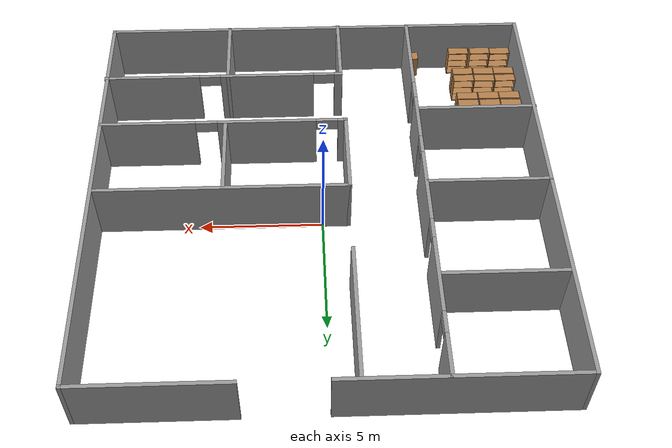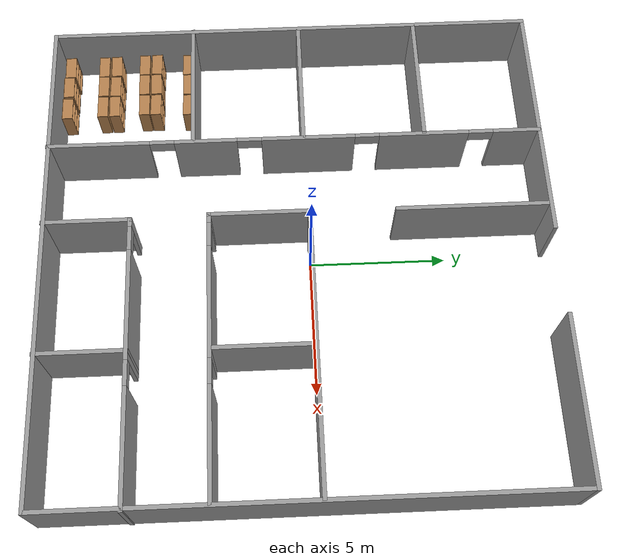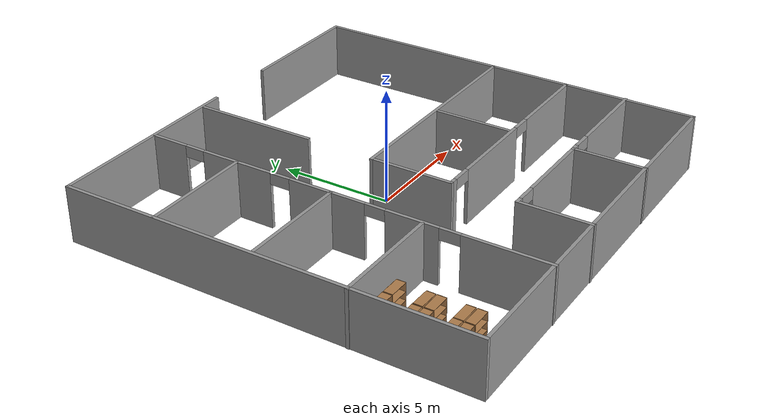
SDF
<sdf version="1.7">
 <world name="default">
  <light name="sun" type="directional">
   <pose>0 0 10 0 -0 0</pose>
   <diffuse>0.8 0.8 0.8 1</diffuse>
   <specular>0.2 0.2 0.2 1</specular>
   <attenuation>
    <range>1000</range>
    <constant>0.9</constant>
    <linear>0.01</linear>
    <quadratic>0.001</quadratic>
   </attenuation>
   <direction>-0.5 0.1 -0.9</direction>
   <spot><inner_angle>0</inner_angle><outer_angle>0</outer_angle><falloff>0</falloff></spot>
  </light>
  <gravity>0 0 -9.8</gravity>
  <magnetic_field>6e-06 2.3e-05 -4.2e-05</magnetic_field>
  <atmosphere type="adiabatic"/>
  <physics type="ode">
   <max_step_size>0.001</max_step_size>
   <real_time_factor>1</real_time_factor>
   <real_time_update_rate>1000</real_time_update_rate>
  </physics>
  <scene><ambient>0.4 0.4 0.4 1</ambient><background>0.7 0.7 0.7 1</background><shadows>1</shadows></scene>
  <spherical_coordinates>
   <surface_model>EARTH_WGS84</surface_model>
   <latitude_deg>0</latitude_deg>
   <longitude_deg>0</longitude_deg>
   <elevation>0</elevation>
   <heading_deg>0</heading_deg>
  </spherical_coordinates>
  <model name="Clinic_Plan">
   <pose>0.061971 -0.423172 0 0 -0 0</pose>
   <link name="Wall_11">
    <pose>-4.13749 -0.011198 0 0 -0 -1.5708</pose>
    <visual name="Wall_11_Visual_0">
     <pose>-8.24062 0 1.25 0 -0 0</pose>
     <geometry><box><size>1.76876 0.15 2.5</size></box></geometry>
     <material>
      <script><uri>file://media/materials/scripts/gazebo.material</uri><name>Gazebo/Grey</name></script>
      <ambient>1 1 1 1</ambient>
     </material>
     <meta><layer>0</layer></meta>
    </visual>
    <collision name="Wall_11_Collision_0">
     <geometry><box><size>1.76876 0.15 2.5</size></box></geometry>
     <pose>-8.24062 0 1.25 0 -0 0</pose>
    </collision>
    <visual name="Wall_11_Visual_1">
     <pose>-4.80135 0 1.25 0 -0 0</pose>
     <geometry><box><size>3.30977 0.15 2.5</size></box></geometry>
     <material>
      <script><uri>file://media/materials/scripts/gazebo.material</uri><name>Gazebo/Grey</name></script>
      <ambient>1 1 1 1</ambient>
     </material>
     <meta><layer>0</layer></meta>
    </visual>
    <collision name="Wall_11_Collision_1">
     <geometry><box><size>3.30977 0.15 2.5</size></box></geometry>
     <pose>-4.80135 0 1.25 0 -0 0</pose>
    </collision>
    <visual name="Wall_11_Visual_2">
     <pose>-0.522188 0 1.25 0 -0 0</pose>
     <geometry><box><size>3.44855 0.15 2.5</size></box></geometry>
     <material>
      <script><uri>file://media/materials/scripts/gazebo.material</uri><name>Gazebo/Grey</name></script>
      <ambient>1 1 1 1</ambient>
     </material>
     <meta><layer>0</layer></meta>
    </visual>
    <collision name="Wall_11_Collision_2">
     <geometry><box><size>3.44855 0.15 2.5</size></box></geometry>
     <pose>-0.522188 0 1.25 0 -0 0</pose>
    </collision>
    <visual name="Wall_11_Visual_3">
     <pose>3.25967 0 1.25 0 -0 0</pose>
     <geometry><box><size>2.31515 0.15 2.5</size></box></geometry>
     <material>
      <script><uri>file://media/materials/scripts/gazebo.material</uri><name>Gazebo/Grey</name></script>
      <ambient>1 1 1 1</ambient>
     </material>
     <meta><layer>0</layer></meta>
    </visual>
    <collision name="Wall_11_Collision_3">
     <geometry><box><size>2.31515 0.15 2.5</size></box></geometry>
     <pose>3.25967 0 1.25 0 -0 0</pose>
    </collision>
    <visual name="Wall_11_Visual_4">
     <pose>7.22112 0 1.25 0 -0 0</pose>
     <geometry><box><size>3.80776 0.15 2.5</size></box></geometry>
     <material>
      <script><uri>file://media/materials/scripts/gazebo.material</uri><name>Gazebo/Grey</name></script>
      <ambient>1 1 1 1</ambient>
     </material>
     <meta><layer>0</layer></meta>
    </visual>
    <collision name="Wall_11_Collision_4">
     <geometry><box><size>3.80776 0.15 2.5</size></box></geometry>
     <pose>7.22112 0 1.25 0 -0 0</pose>
    </collision>
    <visual name="Wall_11_Visual_5">
     <pose>-6.90624 0 2.25 0 -0 0</pose>
     <geometry><box><size>0.9 0.15 0.5</size></box></geometry>
     <material>
      <script><uri>file://media/materials/scripts/gazebo.material</uri><name>Gazebo/Grey</name></script>
      <ambient>1 1 1 1</ambient>
     </material>
     <meta><layer>0</layer></meta>
    </visual>
    <collision name="Wall_11_Collision_5">
     <geometry><box><size>0.9 0.15 0.5</size></box></geometry>
     <pose>-6.90624 0 2.25 0 -0 0</pose>
    </collision>
    <visual name="Wall_11_Visual_6">
     <pose>-2.69646 0 2.25 0 -0 0</pose>
     <geometry><box><size>0.9 0.15 0.5</size></box></geometry>
     <material>
      <script><uri>file://media/materials/scripts/gazebo.material</uri><name>Gazebo/Grey</name></script>
      <ambient>1 1 1 1</ambient>
     </material>
     <meta><layer>0</layer></meta>
    </visual>
    <collision name="Wall_11_Collision_6">
     <geometry><box><size>0.9 0.15 0.5</size></box></geometry>
     <pose>-2.69646 0 2.25 0 -0 0</pose>
    </collision>
    <visual name="Wall_11_Visual_7">
     <pose>1.65209 0 2.25 0 -0 0</pose>
     <geometry><box><size>0.9 0.15 0.5</size></box></geometry>
     <material>
      <script><uri>file://media/materials/scripts/gazebo.material</uri><name>Gazebo/Grey</name></script>
      <ambient>1 1 1 1</ambient>
     </material>
     <meta><layer>0</layer></meta>
    </visual>
    <collision name="Wall_11_Collision_7">
     <geometry><box><size>0.9 0.15 0.5</size></box></geometry>
     <pose>1.65209 0 2.25 0 -0 0</pose>
    </collision>
    <visual name="Wall_11_Visual_8">
     <pose>4.86724 0 2.25 0 -0 0</pose>
     <geometry><box><size>0.9 0.15 0.5</size></box></geometry>
     <material>
      <script><uri>file://media/materials/scripts/gazebo.material</uri><name>Gazebo/Grey</name></script>
      <ambient>1 1 1 1</ambient>
     </material>
     <meta><layer>0</layer></meta>
    </visual>
    <collision name="Wall_11_Collision_8">
     <geometry><box><size>0.9 0.15 0.5</size></box></geometry>
     <pose>4.86724 0 2.25 0 -0 0</pose>
    </collision>
   </link>
   <link name="Wall_15">
    <collision name="Wall_15_Collision">
     <geometry><box><size>5 0.15 2.5</size></box></geometry>
     <pose>0 0 1.25 0 -0 0</pose>
    </collision>
    <visual name="Wall_15_Visual">
     <pose>0 0 1.25 0 -0 0</pose>
     <geometry><box><size>5 0.15 2.5</size></box></geometry>
     <material>
      <script><uri>file://media/materials/scripts/gazebo.material</uri><name>Gazebo/Grey</name></script>
      <ambient>1 1 1 1</ambient>
     </material>
     <meta><layer>0</layer></meta>
    </visual>
    <pose>-6.62954 4.79703 0 0 -0 0</pose>
   </link>
   <link name="Wall_17">
    <collision name="Wall_17_Collision">
     <geometry><box><size>5 0.15 2.5</size></box></geometry>
     <pose>0 0 1.25 0 -0 0</pose>
    </collision>
    <visual name="Wall_17_Visual">
     <pose>0 0 1.25 0 -0 0</pose>
     <geometry><box><size>5 0.15 2.5</size></box></geometry>
     <material>
      <script><uri>file://media/materials/scripts/gazebo.material</uri><name>Gazebo/Grey</name></script>
      <ambient>1 1 1 1</ambient>
     </material>
     <meta><layer>0</layer></meta>
    </visual>
    <pose>-6.62954 0.330853 0 0 -0 0</pose>
   </link>
   <link name="Wall_19">
    <collision name="Wall_19_Collision">
     <geometry><box><size>5 0.15 2.5</size></box></geometry>
     <pose>0 0 1.25 0 -0 0</pose>
    </collision>
    <visual name="Wall_19_Visual">
     <pose>0 0 1.25 0 -0 0</pose>
     <geometry><box><size>5 0.15 2.5</size></box></geometry>
     <material>
      <script><uri>file://media/materials/scripts/gazebo.material</uri><name>Gazebo/Grey</name></script>
      <ambient>1 1 1 1</ambient>
     </material>
     <meta><layer>0</layer></meta>
    </visual>
    <pose>-6.66013 -3.73765 0 0 -0 0</pose>
   </link>
   <link name="Wall_22">
    <collision name="Wall_22_Collision">
     <geometry><box><size>3.25 0.15 2.5</size></box></geometry>
     <pose>0 0 1.25 0 -0 0</pose>
    </collision>
    <visual name="Wall_22_Visual">
     <pose>0 0 1.25 0 -0 0</pose>
     <geometry><box><size>3.25 0.15 2.5</size></box></geometry>
     <material>
      <script><uri>file://media/materials/scripts/gazebo.material</uri><name>Gazebo/Grey</name></script>
      <ambient>1 1 1 1</ambient>
     </material>
     <meta><layer>0</layer></meta>
    </visual>
    <pose>-1.0264 -7.51474 0 0 -0 1.5708</pose>
   </link>
   <link name="Wall_3">
    <collision name="Wall_3_Collision">
     <geometry><box><size>18.25 0.15 2.5</size></box></geometry>
     <pose>0 0 1.25 0 -0 0</pose>
    </collision>
    <visual name="Wall_3_Visual">
     <pose>0 0 1.25 0 -0 0</pose>
     <geometry><box><size>18.25 0.15 2.5</size></box></geometry>
     <material>
      <script><uri>file://media/materials/scripts/gazebo.material</uri><name>Gazebo/Grey</name></script>
      <ambient>1 1 1 1</ambient>
     </material>
     <meta><layer>0</layer></meta>
    </visual>
    <pose>-9.0597 0.014737 0 0 -0 -1.5708</pose>
   </link>
   <link name="Wall_32">
    <pose>4.03513 -5.96146 0 0 -0 0</pose>
    <visual name="Wall_32_Visual_0">
     <pose>-4.9534 0 1.25 0 -0 0</pose>
     <geometry><box><size>0.343205 0.15 2.5</size></box></geometry>
     <material>
      <script><uri>file://media/materials/scripts/gazebo.material</uri><name>Gazebo/Grey</name></script>
      <ambient>1 1 1 1</ambient>
     </material>
     <meta><layer>0</layer></meta>
    </visual>
    <collision name="Wall_32_Collision_0">
     <geometry><box><size>0.343205 0.15 2.5</size></box></geometry>
     <pose>-4.9534 0 1.25 0 -0 0</pose>
    </collision>
    <visual name="Wall_32_Visual_1">
     <pose>-1.87128 0 1.25 0 -0 0</pose>
     <geometry><box><size>4.02104 0.15 2.5</size></box></geometry>
     <material>
      <script><uri>file://media/materials/scripts/gazebo.material</uri><name>Gazebo/Grey</name></script>
      <ambient>1 1 1 1</ambient>
     </material>
     <meta><layer>0</layer></meta>
    </visual>
    <collision name="Wall_32_Collision_1">
     <geometry><box><size>4.02104 0.15 2.5</size></box></geometry>
     <pose>-1.87128 0 1.25 0 -0 0</pose>
    </collision>
    <visual name="Wall_32_Visual_2">
     <pose>3.08212 0 1.25 0 -0 0</pose>
     <geometry><box><size>4.08576 0.15 2.5</size></box></geometry>
     <material>
      <script><uri>file://media/materials/scripts/gazebo.material</uri><name>Gazebo/Grey</name></script>
      <ambient>1 1 1 1</ambient>
     </material>
     <meta><layer>0</layer></meta>
    </visual>
    <collision name="Wall_32_Collision_2">
     <geometry><box><size>4.08576 0.15 2.5</size></box></geometry>
     <pose>3.08212 0 1.25 0 -0 0</pose>
    </collision>
    <visual name="Wall_32_Visual_3">
     <pose>-4.33179 0 2.25 0 -0 0</pose>
     <geometry><box><size>0.9 0.15 0.5</size></box></geometry>
     <material>
      <script><uri>file://media/materials/scripts/gazebo.material</uri><name>Gazebo/Grey</name></script>
      <ambient>1 1 1 1</ambient>
     </material>
     <meta><layer>0</layer></meta>
    </visual>
    <collision name="Wall_32_Collision_3">
     <geometry><box><size>0.9 0.15 0.5</size></box></geometry>
     <pose>-4.33179 0 2.25 0 -0 0</pose>
    </collision>
    <visual name="Wall_32_Visual_4">
     <pose>0.589242 0 2.25 0 -0 0</pose>
     <geometry><box><size>0.9 0.15 0.5</size></box></geometry>
     <material>
      <script><uri>file://media/materials/scripts/gazebo.material</uri><name>Gazebo/Grey</name></script>
      <ambient>1 1 1 1</ambient>
     </material>
     <meta><layer>0</layer></meta>
    </visual>
    <collision name="Wall_32_Collision_4">
     <geometry><box><size>0.9 0.15 0.5</size></box></geometry>
     <pose>0.589242 0 2.25 0 -0 0</pose>
    </collision>
   </link>
   <link name="Wall_34">
    <pose>3.93681 -3.16844 0 0 -0 3.14159</pose>
    <visual name="Wall_34_Visual_0">
     <pose>-3.15181 0 1.25 0 -0 0</pose>
     <geometry><box><size>3.94638 0.15 2.5</size></box></geometry>
     <material>
      <script><uri>file://media/materials/scripts/gazebo.material</uri><name>Gazebo/Grey</name></script>
      <ambient>1 1 1 1</ambient>
     </material>
     <meta><layer>0</layer></meta>
    </visual>
    <collision name="Wall_34_Collision_0">
     <geometry><box><size>3.94638 0.15 2.5</size></box></geometry>
     <pose>-3.15181 0 1.25 0 -0 0</pose>
    </collision>
    <visual name="Wall_34_Visual_1">
     <pose>1.77322 0 1.25 0 -0 0</pose>
     <geometry><box><size>4.10368 0.15 2.5</size></box></geometry>
     <material>
      <script><uri>file://media/materials/scripts/gazebo.material</uri><name>Gazebo/Grey</name></script>
      <ambient>1 1 1 1</ambient>
     </material>
     <meta><layer>0</layer></meta>
    </visual>
    <collision name="Wall_34_Collision_1">
     <geometry><box><size>4.10368 0.15 2.5</size></box></geometry>
     <pose>1.77322 0 1.25 0 -0 0</pose>
    </collision>
    <visual name="Wall_34_Visual_2">
     <pose>4.92503 0 1.25 0 -0 0</pose>
     <geometry><box><size>0.399938 0.15 2.5</size></box></geometry>
     <material>
      <script><uri>file://media/materials/scripts/gazebo.material</uri><name>Gazebo/Grey</name></script>
      <ambient>1 1 1 1</ambient>
     </material>
     <meta><layer>0</layer></meta>
    </visual>
    <collision name="Wall_34_Collision_2">
     <geometry><box><size>0.399938 0.15 2.5</size></box></geometry>
     <pose>4.92503 0 1.25 0 -0 0</pose>
    </collision>
    <visual name="Wall_34_Visual_3">
     <pose>-0.728617 0 2.25 0 -0 0</pose>
     <geometry><box><size>0.9 0.15 0.5</size></box></geometry>
     <material>
      <script><uri>file://media/materials/scripts/gazebo.material</uri><name>Gazebo/Grey</name></script>
      <ambient>1 1 1 1</ambient>
     </material>
     <meta><layer>0</layer></meta>
    </visual>
    <collision name="Wall_34_Collision_3">
     <geometry><box><size>0.9 0.15 0.5</size></box></geometry>
     <pose>-0.728617 0 2.25 0 -0 0</pose>
    </collision>
    <visual name="Wall_34_Visual_4">
     <pose>4.27506 0 2.25 0 -0 0</pose>
     <geometry><box><size>0.9 0.15 0.5</size></box></geometry>
     <material>
      <script><uri>file://media/materials/scripts/gazebo.material</uri><name>Gazebo/Grey</name></script>
      <ambient>1 1 1 1</ambient>
     </material>
     <meta><layer>0</layer></meta>
    </visual>
    <collision name="Wall_34_Collision_4">
     <geometry><box><size>0.9 0.15 0.5</size></box></geometry>
     <pose>4.27506 0 2.25 0 -0 0</pose>
    </collision>
   </link>
   <link name="Wall_36">
    <collision name="Wall_36_Collision">
     <geometry><box><size>3.25 0.15 2.5</size></box></geometry>
     <pose>0 0 1.25 0 -0 0</pose>
    </collision>
    <visual name="Wall_36_Visual">
     <pose>0 0 1.25 0 -0 0</pose>
     <geometry><box><size>3.25 0.15 2.5</size></box></geometry>
     <material>
      <script><uri>file://media/materials/scripts/gazebo.material</uri><name>Gazebo/Grey</name></script>
      <ambient>1 1 1 1</ambient>
     </material>
     <meta><layer>0</layer></meta>
    </visual>
    <pose>3.84891 -7.50761 0 0 -0 -1.5708</pose>
   </link>
   <link name="Wall_38">
    <collision name="Wall_38_Collision">
     <geometry><box><size>10.25 0.15 2.5</size></box></geometry>
     <pose>0 0 1.25 0 -0 0</pose>
    </collision>
    <visual name="Wall_38_Visual">
     <pose>0 0 1.25 0 -0 0</pose>
     <geometry><box><size>10.25 0.15 2.5</size></box></geometry>
     <material>
      <script><uri>file://media/materials/scripts/gazebo.material</uri><name>Gazebo/Grey</name></script>
      <ambient>1 1 1 1</ambient>
     </material>
     <meta><layer>0</layer></meta>
    </visual>
    <pose>3.93681 0.431559 0 0 -0 0</pose>
   </link>
   <link name="Wall_40">
    <collision name="Wall_40_Collision">
     <geometry><box><size>3.5 0.15 2.5</size></box></geometry>
     <pose>0 0 1.25 0 -0 0</pose>
    </collision>
    <visual name="Wall_40_Visual">
     <pose>0 0 1.25 0 -0 0</pose>
     <geometry><box><size>3.5 0.15 2.5</size></box></geometry>
     <material>
      <script><uri>file://media/materials/scripts/gazebo.material</uri><name>Gazebo/Grey</name></script>
      <ambient>1 1 1 1</ambient>
     </material>
     <meta><layer>0</layer></meta>
    </visual>
    <pose>3.87146 -1.3505 0 0 -0 1.5708</pose>
   </link>
   <link name="Wall_43">
    <collision name="Wall_43_Collision">
     <geometry><box><size>3.75 0.15 2.5</size></box></geometry>
     <pose>0 0 1.25 0 -0 0</pose>
    </collision>
    <visual name="Wall_43_Visual">
     <pose>0 0 1.25 0 -0 0</pose>
     <geometry><box><size>3.75 0.15 2.5</size></box></geometry>
     <material>
      <script><uri>file://media/materials/scripts/gazebo.material</uri><name>Gazebo/Grey</name></script>
      <ambient>1 1 1 1</ambient>
     </material>
     <meta><layer>0</layer></meta>
    </visual>
    <pose>-1.11319 -1.36844 0 0 -0 -1.5708</pose>
   </link>
   <link name="Wall_46">
    <collision name="Wall_46_Collision">
     <geometry><box><size>5.5 0.15 2.5</size></box></geometry>
     <pose>0 0 1.25 0 -0 0</pose>
    </collision>
    <visual name="Wall_46_Visual">
     <pose>0 0 1.25 0 -0 0</pose>
     <geometry><box><size>5.5 0.15 2.5</size></box></geometry>
     <material>
      <script><uri>file://media/materials/scripts/gazebo.material</uri><name>Gazebo/Grey</name></script>
      <ambient>1 1 1 1</ambient>
     </material>
     <meta><layer>0</layer></meta>
    </visual>
    <pose>-1.07436 6.24221 0 0 -0 1.5708</pose>
   </link>
   <link name="Wall_48">
    <collision name="Wall_48_Collision">
     <geometry><box><size>6 0.15 2.5</size></box></geometry>
     <pose>0 0 1.25 0 -0 0</pose>
    </collision>
    <visual name="Wall_48_Visual">
     <pose>0 0 1.25 0 -0 0</pose>
     <geometry><box><size>6 0.15 2.5</size></box></geometry>
     <material>
      <script><uri>file://media/materials/scripts/gazebo.material</uri><name>Gazebo/Grey</name></script>
      <ambient>1 1 1 1</ambient>
     </material>
     <meta><layer>0</layer></meta>
    </visual>
    <pose>6.1153 9.06474 0 0 -0 3.14159</pose>
   </link>
   <link name="Wall_5">
    <collision name="Wall_5_Collision">
     <geometry><box><size>18.25 0.15 2.5</size></box></geometry>
     <pose>0 0 1.25 0 -0 0</pose>
    </collision>
    <visual name="Wall_5_Visual">
     <pose>0 0 1.25 0 -0 0</pose>
     <geometry><box><size>18.25 0.15 2.5</size></box></geometry>
     <material>
      <script><uri>file://media/materials/scripts/gazebo.material</uri><name>Gazebo/Grey</name></script>
      <ambient>1 1 1 1</ambient>
     </material>
     <meta><layer>0</layer></meta>
    </visual>
    <pose>-0.0097 -9.03526 0 0 -0 0</pose>
   </link>
   <link name="Wall_50">
    <collision name="Wall_50_Collision">
     <geometry><box><size>9 0.15 2.5</size></box></geometry>
     <pose>0 0 1.25 0 -0 0</pose>
    </collision>
    <visual name="Wall_50_Visual">
     <pose>0 0 1.25 0 -0 0</pose>
     <geometry><box><size>9 0.15 2.5</size></box></geometry>
     <material>
      <script><uri>file://media/materials/scripts/gazebo.material</uri><name>Gazebo/Grey</name></script>
      <ambient>1 1 1 1</ambient>
     </material>
     <meta><layer>0</layer></meta>
    </visual>
    <pose>-4.56024 9.06375 0 0 -0 3.14159</pose>
   </link>
   <link name="Wall_6">
    <collision name="Wall_6_Collision">
     <geometry><box><size>18.25 0.15 2.5</size></box></geometry>
     <pose>0 0 1.25 0 -0 0</pose>
    </collision>
    <visual name="Wall_6_Visual">
     <pose>0 0 1.25 0 -0 0</pose>
     <geometry><box><size>18.25 0.15 2.5</size></box></geometry>
     <material>
      <script><uri>file://media/materials/scripts/gazebo.material</uri><name>Gazebo/Grey</name></script>
      <ambient>1 1 1 1</ambient>
     </material>
     <meta><layer>0</layer></meta>
    </visual>
    <pose>9.0403 0.014737 0 0 -0 1.5708</pose>
   </link>
   <static>1</static>
  </model>
  <model name="bookshelf">
   <static>1</static>
   <link name="link">
    <inertial><mass>1</mass></inertial>
    <collision name="back">
     <pose>0 0.005 0.6 0 -0 0</pose>
     <geometry><box><size>0.9 0.01 1.2</size></box></geometry>
    </collision>
    <visual name="visual1">
     <pose>0 0.005 0.6 0 -0 0</pose>
     <geometry><box><size>0.9 0.01 1.2</size></box></geometry>
     <material>
      <script><uri>file://media/materials/scripts/gazebo.material</uri><name>Gazebo/Wood</name></script>
     </material>
    </visual>
    <collision name="left_side">
     <pose>0.45 -0.195 0.6 0 -0 0</pose>
     <geometry><box><size>0.02 0.4 1.2</size></box></geometry>
    </collision>
    <visual name="visual2">
     <pose>0.45 -0.195 0.6 0 -0 0</pose>
     <geometry><box><size>0.02 0.4 1.2</size></box></geometry>
     <material>
      <script><uri>file://media/materials/scripts/gazebo.material</uri><name>Gazebo/Wood</name></script>
     </material>
    </visual>
    <collision name="right_side">
     <pose>-0.45 -0.195 0.6 0 -0 0</pose>
     <geometry><box><size>0.02 0.4 1.2</size></box></geometry>
    </collision>
    <visual name="visual3">
     <pose>-0.45 -0.195 0.6 0 -0 0</pose>
     <geometry><box><size>0.02 0.4 1.2</size></box></geometry>
     <material>
      <script><uri>file://media/materials/scripts/gazebo.material</uri><name>Gazebo/Wood</name></script>
     </material>
    </visual>
    <collision name="bottom">
     <pose>0 -0.195 0.03 0 -0 0</pose>
     <geometry><box><size>0.88 0.4 0.06</size></box></geometry>
    </collision>
    <visual name="visual4">
     <pose>0 -0.195 0.03 0 -0 0</pose>
     <geometry><box><size>0.88 0.4 0.06</size></box></geometry>
     <material>
      <script><uri>file://media/materials/scripts/gazebo.material</uri><name>Gazebo/Wood</name></script>
     </material>
    </visual>
    <collision name="top">
     <pose>0 -0.195 1.19 0 -0 0</pose>
     <geometry><box><size>0.88 0.4 0.02</size></box></geometry>
    </collision>
    <visual name="visual5">
     <pose>0 -0.195 1.19 0 -0 0</pose>
     <geometry><box><size>0.88 0.4 0.02</size></box></geometry>
     <material>
      <script><uri>file://media/materials/scripts/gazebo.material</uri><name>Gazebo/Wood</name></script>
     </material>
    </visual>
    <collision name="low_shelf">
     <pose>0 -0.195 0.43 0 -0 0</pose>
     <geometry><box><size>0.88 0.4 0.02</size></box></geometry>
    </collision>
    <visual name="visual6">
     <pose>0 -0.195 0.43 0 -0 0</pose>
     <geometry><box><size>0.88 0.4 0.02</size></box></geometry>
     <material>
      <script><uri>file://media/materials/scripts/gazebo.material</uri><name>Gazebo/Wood</name></script>
     </material>
    </visual>
    <collision name="high_shelf">
     <pose>0 -0.195 0.8 0 -0 0</pose>
     <geometry><box><size>0.88 0.4 0.02</size></box></geometry>
    </collision>
    <visual name="visual7">
     <pose>0 -0.195 0.8 0 -0 0</pose>
     <geometry><box><size>0.88 0.4 0.02</size></box></geometry>
     <material>
      <script><uri>file://media/materials/scripts/gazebo.material</uri><name>Gazebo/Wood</name></script>
     </material>
    </visual>
   </link>
   <pose>-6.53627 -4.27883 0 0 -0 0</pose>
  </model>
  <model name="bookshelf_0">
   <static>1</static>
   <link name="link">
    <inertial><mass>1</mass></inertial>
    <collision name="back">
     <pose>0 0.005 0.6 0 -0 0</pose>
     <geometry><box><size>0.9 0.01 1.2</size></box></geometry>
    </collision>
    <visual name="visual1">
     <pose>0 0.005 0.6 0 -0 0</pose>
     <geometry><box><size>0.9 0.01 1.2</size></box></geometry>
     <material>
      <script><uri>file://media/materials/scripts/gazebo.material</uri><name>Gazebo/Wood</name></script>
     </material>
    </visual>
    <collision name="left_side">
     <pose>0.45 -0.195 0.6 0 -0 0</pose>
     <geometry><box><size>0.02 0.4 1.2</size></box></geometry>
    </collision>
    <visual name="visual2">
     <pose>0.45 -0.195 0.6 0 -0 0</pose>
     <geometry><box><size>0.02 0.4 1.2</size></box></geometry>
     <material>
      <script><uri>file://media/materials/scripts/gazebo.material</uri><name>Gazebo/Wood</name></script>
     </material>
    </visual>
    <collision name="right_side">
     <pose>-0.45 -0.195 0.6 0 -0 0</pose>
     <geometry><box><size>0.02 0.4 1.2</size></box></geometry>
    </collision>
    <visual name="visual3">
     <pose>-0.45 -0.195 0.6 0 -0 0</pose>
     <geometry><box><size>0.02 0.4 1.2</size></box></geometry>
     <material>
      <script><uri>file://media/materials/scripts/gazebo.material</uri><name>Gazebo/Wood</name></script>
     </material>
    </visual>
    <collision name="bottom">
     <pose>0 -0.195 0.03 0 -0 0</pose>
     <geometry><box><size>0.88 0.4 0.06</size></box></geometry>
    </collision>
    <visual name="visual4">
     <pose>0 -0.195 0.03 0 -0 0</pose>
     <geometry><box><size>0.88 0.4 0.06</size></box></geometry>
     <material>
      <script><uri>file://media/materials/scripts/gazebo.material</uri><name>Gazebo/Wood</name></script>
     </material>
    </visual>
    <collision name="top">
     <pose>0 -0.195 1.19 0 -0 0</pose>
     <geometry><box><size>0.88 0.4 0.02</size></box></geometry>
    </collision>
    <visual name="visual5">
     <pose>0 -0.195 1.19 0 -0 0</pose>
     <geometry><box><size>0.88 0.4 0.02</size></box></geometry>
     <material>
      <script><uri>file://media/materials/scripts/gazebo.material</uri><name>Gazebo/Wood</name></script>
     </material>
    </visual>
    <collision name="low_shelf">
     <pose>0 -0.195 0.43 0 -0 0</pose>
     <geometry><box><size>0.88 0.4 0.02</size></box></geometry>
    </collision>
    <visual name="visual6">
     <pose>0 -0.195 0.43 0 -0 0</pose>
     <geometry><box><size>0.88 0.4 0.02</size></box></geometry>
     <material>
      <script><uri>file://media/materials/scripts/gazebo.material</uri><name>Gazebo/Wood</name></script>
     </material>
    </visual>
    <collision name="high_shelf">
     <pose>0 -0.195 0.8 0 -0 0</pose>
     <geometry><box><size>0.88 0.4 0.02</size></box></geometry>
    </collision>
    <visual name="visual7">
     <pose>0 -0.195 0.8 0 -0 0</pose>
     <geometry><box><size>0.88 0.4 0.02</size></box></geometry>
     <material>
      <script><uri>file://media/materials/scripts/gazebo.material</uri><name>Gazebo/Wood</name></script>
     </material>
    </visual>
   </link>
   <pose>-7.47578 -4.27956 0 0 -0 0</pose>
  </model>
  <model name="bookshelf_1">
   <static>1</static>
   <link name="link">
    <inertial><mass>1</mass></inertial>
    <collision name="back">
     <pose>0 0.005 0.6 0 -0 0</pose>
     <geometry><box><size>0.9 0.01 1.2</size></box></geometry>
    </collision>
    <visual name="visual1">
     <pose>0 0.005 0.6 0 -0 0</pose>
     <geometry><box><size>0.9 0.01 1.2</size></box></geometry>
     <material>
      <script><uri>file://media/materials/scripts/gazebo.material</uri><name>Gazebo/Wood</name></script>
     </material>
    </visual>
    <collision name="left_side">
     <pose>0.45 -0.195 0.6 0 -0 0</pose>
     <geometry><box><size>0.02 0.4 1.2</size></box></geometry>
    </collision>
    <visual name="visual2">
     <pose>0.45 -0.195 0.6 0 -0 0</pose>
     <geometry><box><size>0.02 0.4 1.2</size></box></geometry>
     <material>
      <script><uri>file://media/materials/scripts/gazebo.material</uri><name>Gazebo/Wood</name></script>
     </material>
    </visual>
    <collision name="right_side">
     <pose>-0.45 -0.195 0.6 0 -0 0</pose>
     <geometry><box><size>0.02 0.4 1.2</size></box></geometry>
    </collision>
    <visual name="visual3">
     <pose>-0.45 -0.195 0.6 0 -0 0</pose>
     <geometry><box><size>0.02 0.4 1.2</size></box></geometry>
     <material>
      <script><uri>file://media/materials/scripts/gazebo.material</uri><name>Gazebo/Wood</name></script>
     </material>
    </visual>
    <collision name="bottom">
     <pose>0 -0.195 0.03 0 -0 0</pose>
     <geometry><box><size>0.88 0.4 0.06</size></box></geometry>
    </collision>
    <visual name="visual4">
     <pose>0 -0.195 0.03 0 -0 0</pose>
     <geometry><box><size>0.88 0.4 0.06</size></box></geometry>
     <material>
      <script><uri>file://media/materials/scripts/gazebo.material</uri><name>Gazebo/Wood</name></script>
     </material>
    </visual>
    <collision name="top">
     <pose>0 -0.195 1.19 0 -0 0</pose>
     <geometry><box><size>0.88 0.4 0.02</size></box></geometry>
    </collision>
    <visual name="visual5">
     <pose>0 -0.195 1.19 0 -0 0</pose>
     <geometry><box><size>0.88 0.4 0.02</size></box></geometry>
     <material>
      <script><uri>file://media/materials/scripts/gazebo.material</uri><name>Gazebo/Wood</name></script>
     </material>
    </visual>
    <collision name="low_shelf">
     <pose>0 -0.195 0.43 0 -0 0</pose>
     <geometry><box><size>0.88 0.4 0.02</size></box></geometry>
    </collision>
    <visual name="visual6">
     <pose>0 -0.195 0.43 0 -0 0</pose>
     <geometry><box><size>0.88 0.4 0.02</size></box></geometry>
     <material>
      <script><uri>file://media/materials/scripts/gazebo.material</uri><name>Gazebo/Wood</name></script>
     </material>
    </visual>
    <collision name="high_shelf">
     <pose>0 -0.195 0.8 0 -0 0</pose>
     <geometry><box><size>0.88 0.4 0.02</size></box></geometry>
    </collision>
    <visual name="visual7">
     <pose>0 -0.195 0.8 0 -0 0</pose>
     <geometry><box><size>0.88 0.4 0.02</size></box></geometry>
     <material>
      <script><uri>file://media/materials/scripts/gazebo.material</uri><name>Gazebo/Wood</name></script>
     </material>
    </visual>
   </link>
   <pose>-8.40078 -4.28984 0 0 -0 0</pose>
  </model>
  <model name="bookshelf_2">
   <static>1</static>
   <link name="link">
    <inertial><mass>1</mass></inertial>
    <collision name="back">
     <pose>0 0.005 0.6 0 -0 0</pose>
     <geometry><box><size>0.9 0.01 1.2</size></box></geometry>
    </collision>
    <visual name="visual1">
     <pose>0 0.005 0.6 0 -0 0</pose>
     <geometry><box><size>0.9 0.01 1.2</size></box></geometry>
     <material>
      <script><uri>file://media/materials/scripts/gazebo.material</uri><name>Gazebo/Wood</name></script>
     </material>
    </visual>
    <collision name="left_side">
     <pose>0.45 -0.195 0.6 0 -0 0</pose>
     <geometry><box><size>0.02 0.4 1.2</size></box></geometry>
    </collision>
    <visual name="visual2">
     <pose>0.45 -0.195 0.6 0 -0 0</pose>
     <geometry><box><size>0.02 0.4 1.2</size></box></geometry>
     <material>
      <script><uri>file://media/materials/scripts/gazebo.material</uri><name>Gazebo/Wood</name></script>
     </material>
    </visual>
    <collision name="right_side">
     <pose>-0.45 -0.195 0.6 0 -0 0</pose>
     <geometry><box><size>0.02 0.4 1.2</size></box></geometry>
    </collision>
    <visual name="visual3">
     <pose>-0.45 -0.195 0.6 0 -0 0</pose>
     <geometry><box><size>0.02 0.4 1.2</size></box></geometry>
     <material>
      <script><uri>file://media/materials/scripts/gazebo.material</uri><name>Gazebo/Wood</name></script>
     </material>
    </visual>
    <collision name="bottom">
     <pose>0 -0.195 0.03 0 -0 0</pose>
     <geometry><box><size>0.88 0.4 0.06</size></box></geometry>
    </collision>
    <visual name="visual4">
     <pose>0 -0.195 0.03 0 -0 0</pose>
     <geometry><box><size>0.88 0.4 0.06</size></box></geometry>
     <material>
      <script><uri>file://media/materials/scripts/gazebo.material</uri><name>Gazebo/Wood</name></script>
     </material>
    </visual>
    <collision name="top">
     <pose>0 -0.195 1.19 0 -0 0</pose>
     <geometry><box><size>0.88 0.4 0.02</size></box></geometry>
    </collision>
    <visual name="visual5">
     <pose>0 -0.195 1.19 0 -0 0</pose>
     <geometry><box><size>0.88 0.4 0.02</size></box></geometry>
     <material>
      <script><uri>file://media/materials/scripts/gazebo.material</uri><name>Gazebo/Wood</name></script>
     </material>
    </visual>
    <collision name="low_shelf">
     <pose>0 -0.195 0.43 0 -0 0</pose>
     <geometry><box><size>0.88 0.4 0.02</size></box></geometry>
    </collision>
    <visual name="visual6">
     <pose>0 -0.195 0.43 0 -0 0</pose>
     <geometry><box><size>0.88 0.4 0.02</size></box></geometry>
     <material>
      <script><uri>file://media/materials/scripts/gazebo.material</uri><name>Gazebo/Wood</name></script>
     </material>
    </visual>
    <collision name="high_shelf">
     <pose>0 -0.195 0.8 0 -0 0</pose>
     <geometry><box><size>0.88 0.4 0.02</size></box></geometry>
    </collision>
    <visual name="visual7">
     <pose>0 -0.195 0.8 0 -0 0</pose>
     <geometry><box><size>0.88 0.4 0.02</size></box></geometry>
     <material>
      <script><uri>file://media/materials/scripts/gazebo.material</uri><name>Gazebo/Wood</name></script>
     </material>
    </visual>
   </link>
   <pose>-8.45393 -6.00213 0 0 -0 0</pose>
  </model>
  <model name="bookshelf_3">
   <static>1</static>
   <link name="link">
    <inertial><mass>1</mass></inertial>
    <collision name="back">
     <pose>0 0.005 0.6 0 -0 0</pose>
     <geometry><box><size>0.9 0.01 1.2</size></box></geometry>
    </collision>
    <visual name="visual1">
     <pose>0 0.005 0.6 0 -0 0</pose>
     <geometry><box><size>0.9 0.01 1.2</size></box></geometry>
     <material>
      <script><uri>file://media/materials/scripts/gazebo.material</uri><name>Gazebo/Wood</name></script>
     </material>
    </visual>
    <collision name="left_side">
     <pose>0.45 -0.195 0.6 0 -0 0</pose>
     <geometry><box><size>0.02 0.4 1.2</size></box></geometry>
    </collision>
    <visual name="visual2">
     <pose>0.45 -0.195 0.6 0 -0 0</pose>
     <geometry><box><size>0.02 0.4 1.2</size></box></geometry>
     <material>
      <script><uri>file://media/materials/scripts/gazebo.material</uri><name>Gazebo/Wood</name></script>
     </material>
    </visual>
    <collision name="right_side">
     <pose>-0.45 -0.195 0.6 0 -0 0</pose>
     <geometry><box><size>0.02 0.4 1.2</size></box></geometry>
    </collision>
    <visual name="visual3">
     <pose>-0.45 -0.195 0.6 0 -0 0</pose>
     <geometry><box><size>0.02 0.4 1.2</size></box></geometry>
     <material>
      <script><uri>file://media/materials/scripts/gazebo.material</uri><name>Gazebo/Wood</name></script>
     </material>
    </visual>
    <collision name="bottom">
     <pose>0 -0.195 0.03 0 -0 0</pose>
     <geometry><box><size>0.88 0.4 0.06</size></box></geometry>
    </collision>
    <visual name="visual4">
     <pose>0 -0.195 0.03 0 -0 0</pose>
     <geometry><box><size>0.88 0.4 0.06</size></box></geometry>
     <material>
      <script><uri>file://media/materials/scripts/gazebo.material</uri><name>Gazebo/Wood</name></script>
     </material>
    </visual>
    <collision name="top">
     <pose>0 -0.195 1.19 0 -0 0</pose>
     <geometry><box><size>0.88 0.4 0.02</size></box></geometry>
    </collision>
    <visual name="visual5">
     <pose>0 -0.195 1.19 0 -0 0</pose>
     <geometry><box><size>0.88 0.4 0.02</size></box></geometry>
     <material>
      <script><uri>file://media/materials/scripts/gazebo.material</uri><name>Gazebo/Wood</name></script>
     </material>
    </visual>
    <collision name="low_shelf">
     <pose>0 -0.195 0.43 0 -0 0</pose>
     <geometry><box><size>0.88 0.4 0.02</size></box></geometry>
    </collision>
    <visual name="visual6">
     <pose>0 -0.195 0.43 0 -0 0</pose>
     <geometry><box><size>0.88 0.4 0.02</size></box></geometry>
     <material>
      <script><uri>file://media/materials/scripts/gazebo.material</uri><name>Gazebo/Wood</name></script>
     </material>
    </visual>
    <collision name="high_shelf">
     <pose>0 -0.195 0.8 0 -0 0</pose>
     <geometry><box><size>0.88 0.4 0.02</size></box></geometry>
    </collision>
    <visual name="visual7">
     <pose>0 -0.195 0.8 0 -0 0</pose>
     <geometry><box><size>0.88 0.4 0.02</size></box></geometry>
     <material>
      <script><uri>file://media/materials/scripts/gazebo.material</uri><name>Gazebo/Wood</name></script>
     </material>
    </visual>
   </link>
   <pose>-7.5302 -6.00242 0 0 -0 0</pose>
  </model>
  <model name="bookshelf_4">
   <static>1</static>
   <link name="link">
    <inertial><mass>1</mass></inertial>
    <collision name="back">
     <pose>0 0.005 0.6 0 -0 0</pose>
     <geometry><box><size>0.9 0.01 1.2</size></box></geometry>
    </collision>
    <visual name="visual1">
     <pose>0 0.005 0.6 0 -0 0</pose>
     <geometry><box><size>0.9 0.01 1.2</size></box></geometry>
     <material>
      <script><uri>file://media/materials/scripts/gazebo.material</uri><name>Gazebo/Wood</name></script>
     </material>
    </visual>
    <collision name="left_side">
     <pose>0.45 -0.195 0.6 0 -0 0</pose>
     <geometry><box><size>0.02 0.4 1.2</size></box></geometry>
    </collision>
    <visual name="visual2">
     <pose>0.45 -0.195 0.6 0 -0 0</pose>
     <geometry><box><size>0.02 0.4 1.2</size></box></geometry>
     <material>
      <script><uri>file://media/materials/scripts/gazebo.material</uri><name>Gazebo/Wood</name></script>
     </material>
    </visual>
    <collision name="right_side">
     <pose>-0.45 -0.195 0.6 0 -0 0</pose>
     <geometry><box><size>0.02 0.4 1.2</size></box></geometry>
    </collision>
    <visual name="visual3">
     <pose>-0.45 -0.195 0.6 0 -0 0</pose>
     <geometry><box><size>0.02 0.4 1.2</size></box></geometry>
     <material>
      <script><uri>file://media/materials/scripts/gazebo.material</uri><name>Gazebo/Wood</name></script>
     </material>
    </visual>
    <collision name="bottom">
     <pose>0 -0.195 0.03 0 -0 0</pose>
     <geometry><box><size>0.88 0.4 0.06</size></box></geometry>
    </collision>
    <visual name="visual4">
     <pose>0 -0.195 0.03 0 -0 0</pose>
     <geometry><box><size>0.88 0.4 0.06</size></box></geometry>
     <material>
      <script><uri>file://media/materials/scripts/gazebo.material</uri><name>Gazebo/Wood</name></script>
     </material>
    </visual>
    <collision name="top">
     <pose>0 -0.195 1.19 0 -0 0</pose>
     <geometry><box><size>0.88 0.4 0.02</size></box></geometry>
    </collision>
    <visual name="visual5">
     <pose>0 -0.195 1.19 0 -0 0</pose>
     <geometry><box><size>0.88 0.4 0.02</size></box></geometry>
     <material>
      <script><uri>file://media/materials/scripts/gazebo.material</uri><name>Gazebo/Wood</name></script>
     </material>
    </visual>
    <collision name="low_shelf">
     <pose>0 -0.195 0.43 0 -0 0</pose>
     <geometry><box><size>0.88 0.4 0.02</size></box></geometry>
    </collision>
    <visual name="visual6">
     <pose>0 -0.195 0.43 0 -0 0</pose>
     <geometry><box><size>0.88 0.4 0.02</size></box></geometry>
     <material>
      <script><uri>file://media/materials/scripts/gazebo.material</uri><name>Gazebo/Wood</name></script>
     </material>
    </visual>
    <collision name="high_shelf">
     <pose>0 -0.195 0.8 0 -0 0</pose>
     <geometry><box><size>0.88 0.4 0.02</size></box></geometry>
    </collision>
    <visual name="visual7">
     <pose>0 -0.195 0.8 0 -0 0</pose>
     <geometry><box><size>0.88 0.4 0.02</size></box></geometry>
     <material>
      <script><uri>file://media/materials/scripts/gazebo.material</uri><name>Gazebo/Wood</name></script>
     </material>
    </visual>
   </link>
   <pose>-6.59095 -5.98674 0 0 -0 0</pose>
  </model>
  <model name="bookshelf_5">
   <static>1</static>
   <link name="link">
    <inertial><mass>1</mass></inertial>
    <collision name="back">
     <pose>0 0.005 0.6 0 -0 0</pose>
     <geometry><box><size>0.9 0.01 1.2</size></box></geometry>
    </collision>
    <visual name="visual1">
     <pose>0 0.005 0.6 0 -0 0</pose>
     <geometry><box><size>0.9 0.01 1.2</size></box></geometry>
     <material>
      <script><uri>file://media/materials/scripts/gazebo.material</uri><name>Gazebo/Wood</name></script>
     </material>
    </visual>
    <collision name="left_side">
     <pose>0.45 -0.195 0.6 0 -0 0</pose>
     <geometry><box><size>0.02 0.4 1.2</size></box></geometry>
    </collision>
    <visual name="visual2">
     <pose>0.45 -0.195 0.6 0 -0 0</pose>
     <geometry><box><size>0.02 0.4 1.2</size></box></geometry>
     <material>
      <script><uri>file://media/materials/scripts/gazebo.material</uri><name>Gazebo/Wood</name></script>
     </material>
    </visual>
    <collision name="right_side">
     <pose>-0.45 -0.195 0.6 0 -0 0</pose>
     <geometry><box><size>0.02 0.4 1.2</size></box></geometry>
    </collision>
    <visual name="visual3">
     <pose>-0.45 -0.195 0.6 0 -0 0</pose>
     <geometry><box><size>0.02 0.4 1.2</size></box></geometry>
     <material>
      <script><uri>file://media/materials/scripts/gazebo.material</uri><name>Gazebo/Wood</name></script>
     </material>
    </visual>
    <collision name="bottom">
     <pose>0 -0.195 0.03 0 -0 0</pose>
     <geometry><box><size>0.88 0.4 0.06</size></box></geometry>
    </collision>
    <visual name="visual4">
     <pose>0 -0.195 0.03 0 -0 0</pose>
     <geometry><box><size>0.88 0.4 0.06</size></box></geometry>
     <material>
      <script><uri>file://media/materials/scripts/gazebo.material</uri><name>Gazebo/Wood</name></script>
     </material>
    </visual>
    <collision name="top">
     <pose>0 -0.195 1.19 0 -0 0</pose>
     <geometry><box><size>0.88 0.4 0.02</size></box></geometry>
    </collision>
    <visual name="visual5">
     <pose>0 -0.195 1.19 0 -0 0</pose>
     <geometry><box><size>0.88 0.4 0.02</size></box></geometry>
     <material>
      <script><uri>file://media/materials/scripts/gazebo.material</uri><name>Gazebo/Wood</name></script>
     </material>
    </visual>
    <collision name="low_shelf">
     <pose>0 -0.195 0.43 0 -0 0</pose>
     <geometry><box><size>0.88 0.4 0.02</size></box></geometry>
    </collision>
    <visual name="visual6">
     <pose>0 -0.195 0.43 0 -0 0</pose>
     <geometry><box><size>0.88 0.4 0.02</size></box></geometry>
     <material>
      <script><uri>file://media/materials/scripts/gazebo.material</uri><name>Gazebo/Wood</name></script>
     </material>
    </visual>
    <collision name="high_shelf">
     <pose>0 -0.195 0.8 0 -0 0</pose>
     <geometry><box><size>0.88 0.4 0.02</size></box></geometry>
    </collision>
    <visual name="visual7">
     <pose>0 -0.195 0.8 0 -0 0</pose>
     <geometry><box><size>0.88 0.4 0.02</size></box></geometry>
     <material>
      <script><uri>file://media/materials/scripts/gazebo.material</uri><name>Gazebo/Wood</name></script>
     </material>
    </visual>
   </link>
   <pose>-8.42282 -7.59521 0 0 -0 0</pose>
  </model>
  <model name="bookshelf_6">
   <static>1</static>
   <link name="link">
    <inertial><mass>1</mass></inertial>
    <collision name="back">
     <pose>0 0.005 0.6 0 -0 0</pose>
     <geometry><box><size>0.9 0.01 1.2</size></box></geometry>
    </collision>
    <visual name="visual1">
     <pose>0 0.005 0.6 0 -0 0</pose>
     <geometry><box><size>0.9 0.01 1.2</size></box></geometry>
     <material>
      <script><uri>file://media/materials/scripts/gazebo.material</uri><name>Gazebo/Wood</name></script>
     </material>
    </visual>
    <collision name="left_side">
     <pose>0.45 -0.195 0.6 0 -0 0</pose>
     <geometry><box><size>0.02 0.4 1.2</size></box></geometry>
    </collision>
    <visual name="visual2">
     <pose>0.45 -0.195 0.6 0 -0 0</pose>
     <geometry><box><size>0.02 0.4 1.2</size></box></geometry>
     <material>
      <script><uri>file://media/materials/scripts/gazebo.material</uri><name>Gazebo/Wood</name></script>
     </material>
    </visual>
    <collision name="right_side">
     <pose>-0.45 -0.195 0.6 0 -0 0</pose>
     <geometry><box><size>0.02 0.4 1.2</size></box></geometry>
    </collision>
    <visual name="visual3">
     <pose>-0.45 -0.195 0.6 0 -0 0</pose>
     <geometry><box><size>0.02 0.4 1.2</size></box></geometry>
     <material>
      <script><uri>file://media/materials/scripts/gazebo.material</uri><name>Gazebo/Wood</name></script>
     </material>
    </visual>
    <collision name="bottom">
     <pose>0 -0.195 0.03 0 -0 0</pose>
     <geometry><box><size>0.88 0.4 0.06</size></box></geometry>
    </collision>
    <visual name="visual4">
     <pose>0 -0.195 0.03 0 -0 0</pose>
     <geometry><box><size>0.88 0.4 0.06</size></box></geometry>
     <material>
      <script><uri>file://media/materials/scripts/gazebo.material</uri><name>Gazebo/Wood</name></script>
     </material>
    </visual>
    <collision name="top">
     <pose>0 -0.195 1.19 0 -0 0</pose>
     <geometry><box><size>0.88 0.4 0.02</size></box></geometry>
    </collision>
    <visual name="visual5">
     <pose>0 -0.195 1.19 0 -0 0</pose>
     <geometry><box><size>0.88 0.4 0.02</size></box></geometry>
     <material>
      <script><uri>file://media/materials/scripts/gazebo.material</uri><name>Gazebo/Wood</name></script>
     </material>
    </visual>
    <collision name="low_shelf">
     <pose>0 -0.195 0.43 0 -0 0</pose>
     <geometry><box><size>0.88 0.4 0.02</size></box></geometry>
    </collision>
    <visual name="visual6">
     <pose>0 -0.195 0.43 0 -0 0</pose>
     <geometry><box><size>0.88 0.4 0.02</size></box></geometry>
     <material>
      <script><uri>file://media/materials/scripts/gazebo.material</uri><name>Gazebo/Wood</name></script>
     </material>
    </visual>
    <collision name="high_shelf">
     <pose>0 -0.195 0.8 0 -0 0</pose>
     <geometry><box><size>0.88 0.4 0.02</size></box></geometry>
    </collision>
    <visual name="visual7">
     <pose>0 -0.195 0.8 0 -0 0</pose>
     <geometry><box><size>0.88 0.4 0.02</size></box></geometry>
     <material>
      <script><uri>file://media/materials/scripts/gazebo.material</uri><name>Gazebo/Wood</name></script>
     </material>
    </visual>
   </link>
   <pose>-7.50944 -7.59535 0 0 -0 0</pose>
  </model>
  <model name="bookshelf_7">
   <static>1</static>
   <link name="link">
    <inertial><mass>1</mass></inertial>
    <collision name="back">
     <pose>0 0.005 0.6 0 -0 0</pose>
     <geometry><box><size>0.9 0.01 1.2</size></box></geometry>
    </collision>
    <visual name="visual1">
     <pose>0 0.005 0.6 0 -0 0</pose>
     <geometry><box><size>0.9 0.01 1.2</size></box></geometry>
     <material>
      <script><uri>file://media/materials/scripts/gazebo.material</uri><name>Gazebo/Wood</name></script>
     </material>
    </visual>
    <collision name="left_side">
     <pose>0.45 -0.195 0.6 0 -0 0</pose>
     <geometry><box><size>0.02 0.4 1.2</size></box></geometry>
    </collision>
    <visual name="visual2">
     <pose>0.45 -0.195 0.6 0 -0 0</pose>
     <geometry><box><size>0.02 0.4 1.2</size></box></geometry>
     <material>
      <script><uri>file://media/materials/scripts/gazebo.material</uri><name>Gazebo/Wood</name></script>
     </material>
    </visual>
    <collision name="right_side">
     <pose>-0.45 -0.195 0.6 0 -0 0</pose>
     <geometry><box><size>0.02 0.4 1.2</size></box></geometry>
    </collision>
    <visual name="visual3">
     <pose>-0.45 -0.195 0.6 0 -0 0</pose>
     <geometry><box><size>0.02 0.4 1.2</size></box></geometry>
     <material>
      <script><uri>file://media/materials/scripts/gazebo.material</uri><name>Gazebo/Wood</name></script>
     </material>
    </visual>
    <collision name="bottom">
     <pose>0 -0.195 0.03 0 -0 0</pose>
     <geometry><box><size>0.88 0.4 0.06</size></box></geometry>
    </collision>
    <visual name="visual4">
     <pose>0 -0.195 0.03 0 -0 0</pose>
     <geometry><box><size>0.88 0.4 0.06</size></box></geometry>
     <material>
      <script><uri>file://media/materials/scripts/gazebo.material</uri><name>Gazebo/Wood</name></script>
     </material>
    </visual>
    <collision name="top">
     <pose>0 -0.195 1.19 0 -0 0</pose>
     <geometry><box><size>0.88 0.4 0.02</size></box></geometry>
    </collision>
    <visual name="visual5">
     <pose>0 -0.195 1.19 0 -0 0</pose>
     <geometry><box><size>0.88 0.4 0.02</size></box></geometry>
     <material>
      <script><uri>file://media/materials/scripts/gazebo.material</uri><name>Gazebo/Wood</name></script>
     </material>
    </visual>
    <collision name="low_shelf">
     <pose>0 -0.195 0.43 0 -0 0</pose>
     <geometry><box><size>0.88 0.4 0.02</size></box></geometry>
    </collision>
    <visual name="visual6">
     <pose>0 -0.195 0.43 0 -0 0</pose>
     <geometry><box><size>0.88 0.4 0.02</size></box></geometry>
     <material>
      <script><uri>file://media/materials/scripts/gazebo.material</uri><name>Gazebo/Wood</name></script>
     </material>
    </visual>
    <collision name="high_shelf">
     <pose>0 -0.195 0.8 0 -0 0</pose>
     <geometry><box><size>0.88 0.4 0.02</size></box></geometry>
    </collision>
    <visual name="visual7">
     <pose>0 -0.195 0.8 0 -0 0</pose>
     <geometry><box><size>0.88 0.4 0.02</size></box></geometry>
     <material>
      <script><uri>file://media/materials/scripts/gazebo.material</uri><name>Gazebo/Wood</name></script>
     </material>
    </visual>
   </link>
   <pose>-6.56754 -7.59716 0 0 -0 0</pose>
  </model>
  <model name="bookshelf_8">
   <static>1</static>
   <link name="link">
    <inertial><mass>1</mass></inertial>
    <collision name="back">
     <pose>0 0.005 0.6 0 -0 0</pose>
     <geometry><box><size>0.9 0.01 1.2</size></box></geometry>
    </collision>
    <visual name="visual1">
     <pose>0 0.005 0.6 0 -0 0</pose>
     <geometry><box><size>0.9 0.01 1.2</size></box></geometry>
     <material>
      <script><uri>file://media/materials/scripts/gazebo.material</uri><name>Gazebo/Wood</name></script>
     </material>
    </visual>
    <collision name="left_side">
     <pose>0.45 -0.195 0.6 0 -0 0</pose>
     <geometry><box><size>0.02 0.4 1.2</size></box></geometry>
    </collision>
    <visual name="visual2">
     <pose>0.45 -0.195 0.6 0 -0 0</pose>
     <geometry><box><size>0.02 0.4 1.2</size></box></geometry>
     <material>
      <script><uri>file://media/materials/scripts/gazebo.material</uri><name>Gazebo/Wood</name></script>
     </material>
    </visual>
    <collision name="right_side">
     <pose>-0.45 -0.195 0.6 0 -0 0</pose>
     <geometry><box><size>0.02 0.4 1.2</size></box></geometry>
    </collision>
    <visual name="visual3">
     <pose>-0.45 -0.195 0.6 0 -0 0</pose>
     <geometry><box><size>0.02 0.4 1.2</size></box></geometry>
     <material>
      <script><uri>file://media/materials/scripts/gazebo.material</uri><name>Gazebo/Wood</name></script>
     </material>
    </visual>
    <collision name="bottom">
     <pose>0 -0.195 0.03 0 -0 0</pose>
     <geometry><box><size>0.88 0.4 0.06</size></box></geometry>
    </collision>
    <visual name="visual4">
     <pose>0 -0.195 0.03 0 -0 0</pose>
     <geometry><box><size>0.88 0.4 0.06</size></box></geometry>
     <material>
      <script><uri>file://media/materials/scripts/gazebo.material</uri><name>Gazebo/Wood</name></script>
     </material>
    </visual>
    <collision name="top">
     <pose>0 -0.195 1.19 0 -0 0</pose>
     <geometry><box><size>0.88 0.4 0.02</size></box></geometry>
    </collision>
    <visual name="visual5">
     <pose>0 -0.195 1.19 0 -0 0</pose>
     <geometry><box><size>0.88 0.4 0.02</size></box></geometry>
     <material>
      <script><uri>file://media/materials/scripts/gazebo.material</uri><name>Gazebo/Wood</name></script>
     </material>
    </visual>
    <collision name="low_shelf">
     <pose>0 -0.195 0.43 0 -0 0</pose>
     <geometry><box><size>0.88 0.4 0.02</size></box></geometry>
    </collision>
    <visual name="visual6">
     <pose>0 -0.195 0.43 0 -0 0</pose>
     <geometry><box><size>0.88 0.4 0.02</size></box></geometry>
     <material>
      <script><uri>file://media/materials/scripts/gazebo.material</uri><name>Gazebo/Wood</name></script>
     </material>
    </visual>
    <collision name="high_shelf">
     <pose>0 -0.195 0.8 0 -0 0</pose>
     <geometry><box><size>0.88 0.4 0.02</size></box></geometry>
    </collision>
    <visual name="visual7">
     <pose>0 -0.195 0.8 0 -0 0</pose>
     <geometry><box><size>0.88 0.4 0.02</size></box></geometry>
     <material>
      <script><uri>file://media/materials/scripts/gazebo.material</uri><name>Gazebo/Wood</name></script>
     </material>
    </visual>
   </link>
   <pose>-6.59153 -5.92618 0 0 -0 3.12455</pose>
  </model>
  <model name="bookshelf_9">
   <static>1</static>
   <link name="link">
    <inertial><mass>1</mass></inertial>
    <collision name="back">
     <pose>0 0.005 0.6 0 -0 0</pose>
     <geometry><box><size>0.9 0.01 1.2</size></box></geometry>
    </collision>
    <visual name="visual1">
     <pose>0 0.005 0.6 0 -0 0</pose>
     <geometry><box><size>0.9 0.01 1.2</size></box></geometry>
     <material>
      <script><uri>file://media/materials/scripts/gazebo.material</uri><name>Gazebo/Wood</name></script>
     </material>
    </visual>
    <collision name="left_side">
     <pose>0.45 -0.195 0.6 0 -0 0</pose>
     <geometry><box><size>0.02 0.4 1.2</size></box></geometry>
    </collision>
    <visual name="visual2">
     <pose>0.45 -0.195 0.6 0 -0 0</pose>
     <geometry><box><size>0.02 0.4 1.2</size></box></geometry>
     <material>
      <script><uri>file://media/materials/scripts/gazebo.material</uri><name>Gazebo/Wood</name></script>
     </material>
    </visual>
    <collision name="right_side">
     <pose>-0.45 -0.195 0.6 0 -0 0</pose>
     <geometry><box><size>0.02 0.4 1.2</size></box></geometry>
    </collision>
    <visual name="visual3">
     <pose>-0.45 -0.195 0.6 0 -0 0</pose>
     <geometry><box><size>0.02 0.4 1.2</size></box></geometry>
     <material>
      <script><uri>file://media/materials/scripts/gazebo.material</uri><name>Gazebo/Wood</name></script>
     </material>
    </visual>
    <collision name="bottom">
     <pose>0 -0.195 0.03 0 -0 0</pose>
     <geometry><box><size>0.88 0.4 0.06</size></box></geometry>
    </collision>
    <visual name="visual4">
     <pose>0 -0.195 0.03 0 -0 0</pose>
     <geometry><box><size>0.88 0.4 0.06</size></box></geometry>
     <material>
      <script><uri>file://media/materials/scripts/gazebo.material</uri><name>Gazebo/Wood</name></script>
     </material>
    </visual>
    <collision name="top">
     <pose>0 -0.195 1.19 0 -0 0</pose>
     <geometry><box><size>0.88 0.4 0.02</size></box></geometry>
    </collision>
    <visual name="visual5">
     <pose>0 -0.195 1.19 0 -0 0</pose>
     <geometry><box><size>0.88 0.4 0.02</size></box></geometry>
     <material>
      <script><uri>file://media/materials/scripts/gazebo.material</uri><name>Gazebo/Wood</name></script>
     </material>
    </visual>
    <collision name="low_shelf">
     <pose>0 -0.195 0.43 0 -0 0</pose>
     <geometry><box><size>0.88 0.4 0.02</size></box></geometry>
    </collision>
    <visual name="visual6">
     <pose>0 -0.195 0.43 0 -0 0</pose>
     <geometry><box><size>0.88 0.4 0.02</size></box></geometry>
     <material>
      <script><uri>file://media/materials/scripts/gazebo.material</uri><name>Gazebo/Wood</name></script>
     </material>
    </visual>
    <collision name="high_shelf">
     <pose>0 -0.195 0.8 0 -0 0</pose>
     <geometry><box><size>0.88 0.4 0.02</size></box></geometry>
    </collision>
    <visual name="visual7">
     <pose>0 -0.195 0.8 0 -0 0</pose>
     <geometry><box><size>0.88 0.4 0.02</size></box></geometry>
     <material>
      <script><uri>file://media/materials/scripts/gazebo.material</uri><name>Gazebo/Wood</name></script>
     </material>
    </visual>
   </link>
   <pose>-7.53023 -5.92154 0 0 0 -3.12005</pose>
  </model>
  <model name="bookshelf_10">
   <static>1</static>
   <link name="link">
    <inertial><mass>1</mass></inertial>
    <collision name="back">
     <pose>0 0.005 0.6 0 -0 0</pose>
     <geometry><box><size>0.9 0.01 1.2</size></box></geometry>
    </collision>
    <visual name="visual1">
     <pose>0 0.005 0.6 0 -0 0</pose>
     <geometry><box><size>0.9 0.01 1.2</size></box></geometry>
     <material>
      <script><uri>file://media/materials/scripts/gazebo.material</uri><name>Gazebo/Wood</name></script>
     </material>
    </visual>
    <collision name="left_side">
     <pose>0.45 -0.195 0.6 0 -0 0</pose>
     <geometry><box><size>0.02 0.4 1.2</size></box></geometry>
    </collision>
    <visual name="visual2">
     <pose>0.45 -0.195 0.6 0 -0 0</pose>
     <geometry><box><size>0.02 0.4 1.2</size></box></geometry>
     <material>
      <script><uri>file://media/materials/scripts/gazebo.material</uri><name>Gazebo/Wood</name></script>
     </material>
    </visual>
    <collision name="right_side">
     <pose>-0.45 -0.195 0.6 0 -0 0</pose>
     <geometry><box><size>0.02 0.4 1.2</size></box></geometry>
    </collision>
    <visual name="visual3">
     <pose>-0.45 -0.195 0.6 0 -0 0</pose>
     <geometry><box><size>0.02 0.4 1.2</size></box></geometry>
     <material>
      <script><uri>file://media/materials/scripts/gazebo.material</uri><name>Gazebo/Wood</name></script>
     </material>
    </visual>
    <collision name="bottom">
     <pose>0 -0.195 0.03 0 -0 0</pose>
     <geometry><box><size>0.88 0.4 0.06</size></box></geometry>
    </collision>
    <visual name="visual4">
     <pose>0 -0.195 0.03 0 -0 0</pose>
     <geometry><box><size>0.88 0.4 0.06</size></box></geometry>
     <material>
      <script><uri>file://media/materials/scripts/gazebo.material</uri><name>Gazebo/Wood</name></script>
     </material>
    </visual>
    <collision name="top">
     <pose>0 -0.195 1.19 0 -0 0</pose>
     <geometry><box><size>0.88 0.4 0.02</size></box></geometry>
    </collision>
    <visual name="visual5">
     <pose>0 -0.195 1.19 0 -0 0</pose>
     <geometry><box><size>0.88 0.4 0.02</size></box></geometry>
     <material>
      <script><uri>file://media/materials/scripts/gazebo.material</uri><name>Gazebo/Wood</name></script>
     </material>
    </visual>
    <collision name="low_shelf">
     <pose>0 -0.195 0.43 0 -0 0</pose>
     <geometry><box><size>0.88 0.4 0.02</size></box></geometry>
    </collision>
    <visual name="visual6">
     <pose>0 -0.195 0.43 0 -0 0</pose>
     <geometry><box><size>0.88 0.4 0.02</size></box></geometry>
     <material>
      <script><uri>file://media/materials/scripts/gazebo.material</uri><name>Gazebo/Wood</name></script>
     </material>
    </visual>
    <collision name="high_shelf">
     <pose>0 -0.195 0.8 0 -0 0</pose>
     <geometry><box><size>0.88 0.4 0.02</size></box></geometry>
    </collision>
    <visual name="visual7">
     <pose>0 -0.195 0.8 0 -0 0</pose>
     <geometry><box><size>0.88 0.4 0.02</size></box></geometry>
     <material>
      <script><uri>file://media/materials/scripts/gazebo.material</uri><name>Gazebo/Wood</name></script>
     </material>
    </visual>
   </link>
   <pose>-8.46669 -5.91075 0 0 -0 3.12391</pose>
  </model>
  <model name="bookshelf_11">
   <static>1</static>
   <link name="link">
    <inertial><mass>1</mass></inertial>
    <collision name="back">
     <pose>0 0.005 0.6 0 -0 0</pose>
     <geometry><box><size>0.9 0.01 1.2</size></box></geometry>
    </collision>
    <visual name="visual1">
     <pose>0 0.005 0.6 0 -0 0</pose>
     <geometry><box><size>0.9 0.01 1.2</size></box></geometry>
     <material>
      <script><uri>file://media/materials/scripts/gazebo.material</uri><name>Gazebo/Wood</name></script>
     </material>
    </visual>
    <collision name="left_side">
     <pose>0.45 -0.195 0.6 0 -0 0</pose>
     <geometry><box><size>0.02 0.4 1.2</size></box></geometry>
    </collision>
    <visual name="visual2">
     <pose>0.45 -0.195 0.6 0 -0 0</pose>
     <geometry><box><size>0.02 0.4 1.2</size></box></geometry>
     <material>
      <script><uri>file://media/materials/scripts/gazebo.material</uri><name>Gazebo/Wood</name></script>
     </material>
    </visual>
    <collision name="right_side">
     <pose>-0.45 -0.195 0.6 0 -0 0</pose>
     <geometry><box><size>0.02 0.4 1.2</size></box></geometry>
    </collision>
    <visual name="visual3">
     <pose>-0.45 -0.195 0.6 0 -0 0</pose>
     <geometry><box><size>0.02 0.4 1.2</size></box></geometry>
     <material>
      <script><uri>file://media/materials/scripts/gazebo.material</uri><name>Gazebo/Wood</name></script>
     </material>
    </visual>
    <collision name="bottom">
     <pose>0 -0.195 0.03 0 -0 0</pose>
     <geometry><box><size>0.88 0.4 0.06</size></box></geometry>
    </collision>
    <visual name="visual4">
     <pose>0 -0.195 0.03 0 -0 0</pose>
     <geometry><box><size>0.88 0.4 0.06</size></box></geometry>
     <material>
      <script><uri>file://media/materials/scripts/gazebo.material</uri><name>Gazebo/Wood</name></script>
     </material>
    </visual>
    <collision name="top">
     <pose>0 -0.195 1.19 0 -0 0</pose>
     <geometry><box><size>0.88 0.4 0.02</size></box></geometry>
    </collision>
    <visual name="visual5">
     <pose>0 -0.195 1.19 0 -0 0</pose>
     <geometry><box><size>0.88 0.4 0.02</size></box></geometry>
     <material>
      <script><uri>file://media/materials/scripts/gazebo.material</uri><name>Gazebo/Wood</name></script>
     </material>
    </visual>
    <collision name="low_shelf">
     <pose>0 -0.195 0.43 0 -0 0</pose>
     <geometry><box><size>0.88 0.4 0.02</size></box></geometry>
    </collision>
    <visual name="visual6">
     <pose>0 -0.195 0.43 0 -0 0</pose>
     <geometry><box><size>0.88 0.4 0.02</size></box></geometry>
     <material>
      <script><uri>file://media/materials/scripts/gazebo.material</uri><name>Gazebo/Wood</name></script>
     </material>
    </visual>
    <collision name="high_shelf">
     <pose>0 -0.195 0.8 0 -0 0</pose>
     <geometry><box><size>0.88 0.4 0.02</size></box></geometry>
    </collision>
    <visual name="visual7">
     <pose>0 -0.195 0.8 0 -0 0</pose>
     <geometry><box><size>0.88 0.4 0.02</size></box></geometry>
     <material>
      <script><uri>file://media/materials/scripts/gazebo.material</uri><name>Gazebo/Wood</name></script>
     </material>
    </visual>
   </link>
   <pose>-6.56652 -7.52688 0 0 0 -3.13362</pose>
  </model>
  <model name="bookshelf_12">
   <static>1</static>
   <link name="link">
    <inertial><mass>1</mass></inertial>
    <collision name="back">
     <pose>0 0.005 0.6 0 -0 0</pose>
     <geometry><box><size>0.9 0.01 1.2</size></box></geometry>
    </collision>
    <visual name="visual1">
     <pose>0 0.005 0.6 0 -0 0</pose>
     <geometry><box><size>0.9 0.01 1.2</size></box></geometry>
     <material>
      <script><uri>file://media/materials/scripts/gazebo.material</uri><name>Gazebo/Wood</name></script>
     </material>
    </visual>
    <collision name="left_side">
     <pose>0.45 -0.195 0.6 0 -0 0</pose>
     <geometry><box><size>0.02 0.4 1.2</size></box></geometry>
    </collision>
    <visual name="visual2">
     <pose>0.45 -0.195 0.6 0 -0 0</pose>
     <geometry><box><size>0.02 0.4 1.2</size></box></geometry>
     <material>
      <script><uri>file://media/materials/scripts/gazebo.material</uri><name>Gazebo/Wood</name></script>
     </material>
    </visual>
    <collision name="right_side">
     <pose>-0.45 -0.195 0.6 0 -0 0</pose>
     <geometry><box><size>0.02 0.4 1.2</size></box></geometry>
    </collision>
    <visual name="visual3">
     <pose>-0.45 -0.195 0.6 0 -0 0</pose>
     <geometry><box><size>0.02 0.4 1.2</size></box></geometry>
     <material>
      <script><uri>file://media/materials/scripts/gazebo.material</uri><name>Gazebo/Wood</name></script>
     </material>
    </visual>
    <collision name="bottom">
     <pose>0 -0.195 0.03 0 -0 0</pose>
     <geometry><box><size>0.88 0.4 0.06</size></box></geometry>
    </collision>
    <visual name="visual4">
     <pose>0 -0.195 0.03 0 -0 0</pose>
     <geometry><box><size>0.88 0.4 0.06</size></box></geometry>
     <material>
      <script><uri>file://media/materials/scripts/gazebo.material</uri><name>Gazebo/Wood</name></script>
     </material>
    </visual>
    <collision name="top">
     <pose>0 -0.195 1.19 0 -0 0</pose>
     <geometry><box><size>0.88 0.4 0.02</size></box></geometry>
    </collision>
    <visual name="visual5">
     <pose>0 -0.195 1.19 0 -0 0</pose>
     <geometry><box><size>0.88 0.4 0.02</size></box></geometry>
     <material>
      <script><uri>file://media/materials/scripts/gazebo.material</uri><name>Gazebo/Wood</name></script>
     </material>
    </visual>
    <collision name="low_shelf">
     <pose>0 -0.195 0.43 0 -0 0</pose>
     <geometry><box><size>0.88 0.4 0.02</size></box></geometry>
    </collision>
    <visual name="visual6">
     <pose>0 -0.195 0.43 0 -0 0</pose>
     <geometry><box><size>0.88 0.4 0.02</size></box></geometry>
     <material>
      <script><uri>file://media/materials/scripts/gazebo.material</uri><name>Gazebo/Wood</name></script>
     </material>
    </visual>
    <collision name="high_shelf">
     <pose>0 -0.195 0.8 0 -0 0</pose>
     <geometry><box><size>0.88 0.4 0.02</size></box></geometry>
    </collision>
    <visual name="visual7">
     <pose>0 -0.195 0.8 0 -0 0</pose>
     <geometry><box><size>0.88 0.4 0.02</size></box></geometry>
     <material>
      <script><uri>file://media/materials/scripts/gazebo.material</uri><name>Gazebo/Wood</name></script>
     </material>
    </visual>
   </link>
   <pose>-7.49522 -7.51776 0 0 -0 3.13394</pose>
  </model>
  <model name="bookshelf_13">
   <static>1</static>
   <link name="link">
    <inertial><mass>1</mass></inertial>
    <collision name="back">
     <pose>0 0.005 0.6 0 -0 0</pose>
     <geometry><box><size>0.9 0.01 1.2</size></box></geometry>
    </collision>
    <visual name="visual1">
     <pose>0 0.005 0.6 0 -0 0</pose>
     <geometry><box><size>0.9 0.01 1.2</size></box></geometry>
     <material>
      <script><uri>file://media/materials/scripts/gazebo.material</uri><name>Gazebo/Wood</name></script>
     </material>
    </visual>
    <collision name="left_side">
     <pose>0.45 -0.195 0.6 0 -0 0</pose>
     <geometry><box><size>0.02 0.4 1.2</size></box></geometry>
    </collision>
    <visual name="visual2">
     <pose>0.45 -0.195 0.6 0 -0 0</pose>
     <geometry><box><size>0.02 0.4 1.2</size></box></geometry>
     <material>
      <script><uri>file://media/materials/scripts/gazebo.material</uri><name>Gazebo/Wood</name></script>
     </material>
    </visual>
    <collision name="right_side">
     <pose>-0.45 -0.195 0.6 0 -0 0</pose>
     <geometry><box><size>0.02 0.4 1.2</size></box></geometry>
    </collision>
    <visual name="visual3">
     <pose>-0.45 -0.195 0.6 0 -0 0</pose>
     <geometry><box><size>0.02 0.4 1.2</size></box></geometry>
     <material>
      <script><uri>file://media/materials/scripts/gazebo.material</uri><name>Gazebo/Wood</name></script>
     </material>
    </visual>
    <collision name="bottom">
     <pose>0 -0.195 0.03 0 -0 0</pose>
     <geometry><box><size>0.88 0.4 0.06</size></box></geometry>
    </collision>
    <visual name="visual4">
     <pose>0 -0.195 0.03 0 -0 0</pose>
     <geometry><box><size>0.88 0.4 0.06</size></box></geometry>
     <material>
      <script><uri>file://media/materials/scripts/gazebo.material</uri><name>Gazebo/Wood</name></script>
     </material>
    </visual>
    <collision name="top">
     <pose>0 -0.195 1.19 0 -0 0</pose>
     <geometry><box><size>0.88 0.4 0.02</size></box></geometry>
    </collision>
    <visual name="visual5">
     <pose>0 -0.195 1.19 0 -0 0</pose>
     <geometry><box><size>0.88 0.4 0.02</size></box></geometry>
     <material>
      <script><uri>file://media/materials/scripts/gazebo.material</uri><name>Gazebo/Wood</name></script>
     </material>
    </visual>
    <collision name="low_shelf">
     <pose>0 -0.195 0.43 0 -0 0</pose>
     <geometry><box><size>0.88 0.4 0.02</size></box></geometry>
    </collision>
    <visual name="visual6">
     <pose>0 -0.195 0.43 0 -0 0</pose>
     <geometry><box><size>0.88 0.4 0.02</size></box></geometry>
     <material>
      <script><uri>file://media/materials/scripts/gazebo.material</uri><name>Gazebo/Wood</name></script>
     </material>
    </visual>
    <collision name="high_shelf">
     <pose>0 -0.195 0.8 0 -0 0</pose>
     <geometry><box><size>0.88 0.4 0.02</size></box></geometry>
    </collision>
    <visual name="visual7">
     <pose>0 -0.195 0.8 0 -0 0</pose>
     <geometry><box><size>0.88 0.4 0.02</size></box></geometry>
     <material>
      <script><uri>file://media/materials/scripts/gazebo.material</uri><name>Gazebo/Wood</name></script>
     </material>
    </visual>
   </link>
   <pose>-8.42123 -7.50347 0 0 0 -3.11299</pose>
  </model>
  <model name="bookshelf_14">
   <static>1</static>
   <link name="link">
    <inertial><mass>1</mass></inertial>
    <collision name="back">
     <pose>0 0.005 0.6 0 -0 0</pose>
     <geometry><box><size>0.9 0.01 1.2</size></box></geometry>
    </collision>
    <visual name="visual1">
     <pose>0 0.005 0.6 0 -0 0</pose>
     <geometry><box><size>0.9 0.01 1.2</size></box></geometry>
     <material>
      <script><uri>file://media/materials/scripts/gazebo.material</uri><name>Gazebo/Wood</name></script>
     </material>
    </visual>
    <collision name="left_side">
     <pose>0.45 -0.195 0.6 0 -0 0</pose>
     <geometry><box><size>0.02 0.4 1.2</size></box></geometry>
    </collision>
    <visual name="visual2">
     <pose>0.45 -0.195 0.6 0 -0 0</pose>
     <geometry><box><size>0.02 0.4 1.2</size></box></geometry>
     <material>
      <script><uri>file://media/materials/scripts/gazebo.material</uri><name>Gazebo/Wood</name></script>
     </material>
    </visual>
    <collision name="right_side">
     <pose>-0.45 -0.195 0.6 0 -0 0</pose>
     <geometry><box><size>0.02 0.4 1.2</size></box></geometry>
    </collision>
    <visual name="visual3">
     <pose>-0.45 -0.195 0.6 0 -0 0</pose>
     <geometry><box><size>0.02 0.4 1.2</size></box></geometry>
     <material>
      <script><uri>file://media/materials/scripts/gazebo.material</uri><name>Gazebo/Wood</name></script>
     </material>
    </visual>
    <collision name="bottom">
     <pose>0 -0.195 0.03 0 -0 0</pose>
     <geometry><box><size>0.88 0.4 0.06</size></box></geometry>
    </collision>
    <visual name="visual4">
     <pose>0 -0.195 0.03 0 -0 0</pose>
     <geometry><box><size>0.88 0.4 0.06</size></box></geometry>
     <material>
      <script><uri>file://media/materials/scripts/gazebo.material</uri><name>Gazebo/Wood</name></script>
     </material>
    </visual>
    <collision name="top">
     <pose>0 -0.195 1.19 0 -0 0</pose>
     <geometry><box><size>0.88 0.4 0.02</size></box></geometry>
    </collision>
    <visual name="visual5">
     <pose>0 -0.195 1.19 0 -0 0</pose>
     <geometry><box><size>0.88 0.4 0.02</size></box></geometry>
     <material>
      <script><uri>file://media/materials/scripts/gazebo.material</uri><name>Gazebo/Wood</name></script>
     </material>
    </visual>
    <collision name="low_shelf">
     <pose>0 -0.195 0.43 0 -0 0</pose>
     <geometry><box><size>0.88 0.4 0.02</size></box></geometry>
    </collision>
    <visual name="visual6">
     <pose>0 -0.195 0.43 0 -0 0</pose>
     <geometry><box><size>0.88 0.4 0.02</size></box></geometry>
     <material>
      <script><uri>file://media/materials/scripts/gazebo.material</uri><name>Gazebo/Wood</name></script>
     </material>
    </visual>
    <collision name="high_shelf">
     <pose>0 -0.195 0.8 0 -0 0</pose>
     <geometry><box><size>0.88 0.4 0.02</size></box></geometry>
    </collision>
    <visual name="visual7">
     <pose>0 -0.195 0.8 0 -0 0</pose>
     <geometry><box><size>0.88 0.4 0.02</size></box></geometry>
     <material>
      <script><uri>file://media/materials/scripts/gazebo.material</uri><name>Gazebo/Wood</name></script>
     </material>
    </visual>
   </link>
   <pose>-6.53247 -9.35794 0 0 0 -3.13133</pose>
  </model>
  <model name="bookshelf_15">
   <static>1</static>
   <link name="link">
    <inertial><mass>1</mass></inertial>
    <collision name="back">
     <pose>0 0.005 0.6 0 -0 0</pose>
     <geometry><box><size>0.9 0.01 1.2</size></box></geometry>
    </collision>
    <visual name="visual1">
     <pose>0 0.005 0.6 0 -0 0</pose>
     <geometry><box><size>0.9 0.01 1.2</size></box></geometry>
     <material>
      <script><uri>file://media/materials/scripts/gazebo.material</uri><name>Gazebo/Wood</name></script>
     </material>
    </visual>
    <collision name="left_side">
     <pose>0.45 -0.195 0.6 0 -0 0</pose>
     <geometry><box><size>0.02 0.4 1.2</size></box></geometry>
    </collision>
    <visual name="visual2">
     <pose>0.45 -0.195 0.6 0 -0 0</pose>
     <geometry><box><size>0.02 0.4 1.2</size></box></geometry>
     <material>
      <script><uri>file://media/materials/scripts/gazebo.material</uri><name>Gazebo/Wood</name></script>
     </material>
    </visual>
    <collision name="right_side">
     <pose>-0.45 -0.195 0.6 0 -0 0</pose>
     <geometry><box><size>0.02 0.4 1.2</size></box></geometry>
    </collision>
    <visual name="visual3">
     <pose>-0.45 -0.195 0.6 0 -0 0</pose>
     <geometry><box><size>0.02 0.4 1.2</size></box></geometry>
     <material>
      <script><uri>file://media/materials/scripts/gazebo.material</uri><name>Gazebo/Wood</name></script>
     </material>
    </visual>
    <collision name="bottom">
     <pose>0 -0.195 0.03 0 -0 0</pose>
     <geometry><box><size>0.88 0.4 0.06</size></box></geometry>
    </collision>
    <visual name="visual4">
     <pose>0 -0.195 0.03 0 -0 0</pose>
     <geometry><box><size>0.88 0.4 0.06</size></box></geometry>
     <material>
      <script><uri>file://media/materials/scripts/gazebo.material</uri><name>Gazebo/Wood</name></script>
     </material>
    </visual>
    <collision name="top">
     <pose>0 -0.195 1.19 0 -0 0</pose>
     <geometry><box><size>0.88 0.4 0.02</size></box></geometry>
    </collision>
    <visual name="visual5">
     <pose>0 -0.195 1.19 0 -0 0</pose>
     <geometry><box><size>0.88 0.4 0.02</size></box></geometry>
     <material>
      <script><uri>file://media/materials/scripts/gazebo.material</uri><name>Gazebo/Wood</name></script>
     </material>
    </visual>
    <collision name="low_shelf">
     <pose>0 -0.195 0.43 0 -0 0</pose>
     <geometry><box><size>0.88 0.4 0.02</size></box></geometry>
    </collision>
    <visual name="visual6">
     <pose>0 -0.195 0.43 0 -0 0</pose>
     <geometry><box><size>0.88 0.4 0.02</size></box></geometry>
     <material>
      <script><uri>file://media/materials/scripts/gazebo.material</uri><name>Gazebo/Wood</name></script>
     </material>
    </visual>
    <collision name="high_shelf">
     <pose>0 -0.195 0.8 0 -0 0</pose>
     <geometry><box><size>0.88 0.4 0.02</size></box></geometry>
    </collision>
    <visual name="visual7">
     <pose>0 -0.195 0.8 0 -0 0</pose>
     <geometry><box><size>0.88 0.4 0.02</size></box></geometry>
     <material>
      <script><uri>file://media/materials/scripts/gazebo.material</uri><name>Gazebo/Wood</name></script>
     </material>
    </visual>
   </link>
   <pose>-7.51645 -9.34879 0 0 -0 -3.12813</pose>
  </model>
  <model name="bookshelf_16">
   <static>1</static>
   <link name="link">
    <inertial><mass>1</mass></inertial>
    <collision name="back">
     <pose>0 0.005 0.6 0 -0 0</pose>
     <geometry><box><size>0.9 0.01 1.2</size></box></geometry>
    </collision>
    <visual name="visual1">
     <pose>0 0.005 0.6 0 -0 0</pose>
     <geometry><box><size>0.9 0.01 1.2</size></box></geometry>
     <material>
      <script><uri>file://media/materials/scripts/gazebo.material</uri><name>Gazebo/Wood</name></script>
     </material>
    </visual>
    <collision name="left_side">
     <pose>0.45 -0.195 0.6 0 -0 0</pose>
     <geometry><box><size>0.02 0.4 1.2</size></box></geometry>
    </collision>
    <visual name="visual2">
     <pose>0.45 -0.195 0.6 0 -0 0</pose>
     <geometry><box><size>0.02 0.4 1.2</size></box></geometry>
     <material>
      <script><uri>file://media/materials/scripts/gazebo.material</uri><name>Gazebo/Wood</name></script>
     </material>
    </visual>
    <collision name="right_side">
     <pose>-0.45 -0.195 0.6 0 -0 0</pose>
     <geometry><box><size>0.02 0.4 1.2</size></box></geometry>
    </collision>
    <visual name="visual3">
     <pose>-0.45 -0.195 0.6 0 -0 0</pose>
     <geometry><box><size>0.02 0.4 1.2</size></box></geometry>
     <material>
      <script><uri>file://media/materials/scripts/gazebo.material</uri><name>Gazebo/Wood</name></script>
     </material>
    </visual>
    <collision name="bottom">
     <pose>0 -0.195 0.03 0 -0 0</pose>
     <geometry><box><size>0.88 0.4 0.06</size></box></geometry>
    </collision>
    <visual name="visual4">
     <pose>0 -0.195 0.03 0 -0 0</pose>
     <geometry><box><size>0.88 0.4 0.06</size></box></geometry>
     <material>
      <script><uri>file://media/materials/scripts/gazebo.material</uri><name>Gazebo/Wood</name></script>
     </material>
    </visual>
    <collision name="top">
     <pose>0 -0.195 1.19 0 -0 0</pose>
     <geometry><box><size>0.88 0.4 0.02</size></box></geometry>
    </collision>
    <visual name="visual5">
     <pose>0 -0.195 1.19 0 -0 0</pose>
     <geometry><box><size>0.88 0.4 0.02</size></box></geometry>
     <material>
      <script><uri>file://media/materials/scripts/gazebo.material</uri><name>Gazebo/Wood</name></script>
     </material>
    </visual>
    <collision name="low_shelf">
     <pose>0 -0.195 0.43 0 -0 0</pose>
     <geometry><box><size>0.88 0.4 0.02</size></box></geometry>
    </collision>
    <visual name="visual6">
     <pose>0 -0.195 0.43 0 -0 0</pose>
     <geometry><box><size>0.88 0.4 0.02</size></box></geometry>
     <material>
      <script><uri>file://media/materials/scripts/gazebo.material</uri><name>Gazebo/Wood</name></script>
     </material>
    </visual>
    <collision name="high_shelf">
     <pose>0 -0.195 0.8 0 -0 0</pose>
     <geometry><box><size>0.88 0.4 0.02</size></box></geometry>
    </collision>
    <visual name="visual7">
     <pose>0 -0.195 0.8 0 -0 0</pose>
     <geometry><box><size>0.88 0.4 0.02</size></box></geometry>
     <material>
      <script><uri>file://media/materials/scripts/gazebo.material</uri><name>Gazebo/Wood</name></script>
     </material>
    </visual>
   </link>
   <pose>-8.4343 -9.31458 0 0 0 -3.12814</pose>
  </model>
  <model name="cabinet">
   <static>1</static>
   <link name="cabinet_bottom_plate">
    <inertial>
     <pose>0 0 -1 0 -0 0</pose>
     <inertia><ixx>2.05</ixx><ixy>0</ixy><ixz>0</ixz><iyy>2.05</iyy><iyz>0</iyz><izz>2.05</izz></inertia>
     <mass>25</mass>
    </inertial>
    <collision name="cabinet_bottom_plate_geom">
     <pose>0 0 0.01 0 -0 0</pose>
     <geometry><box><size>0.45 0.45 0.02</size></box></geometry>
    </collision>
    <visual name="cabinet_bottom_plate_geom_visual">
     <pose>0 0 0.01 0 -0 0</pose>
     <geometry><box><size>0.45 0.45 0.02</size></box></geometry>
     <material>
      <script><uri>file://media/materials/scripts/gazebo.material</uri><name>Gazebo/Wood</name></script>
     </material>
    </visual>
    <collision name="cabinet_bottom_plate_geom_cabinet_back_plate">
     <pose>0.235 0 0.51 0 -0 0</pose>
     <geometry><box><size>0.02 0.45 1.02</size></box></geometry>
    </collision>
    <visual name="cabinet_bottom_plate_geom_cabinet_back_plate_visual">
     <pose>0.235 0 0.51 0 -0 0</pose>
     <geometry><box><size>0.02 0.45 1.02</size></box></geometry>
     <material>
      <script><uri>file://media/materials/scripts/gazebo.material</uri><name>Gazebo/Wood</name></script>
     </material>
    </visual>
    <collision name="cabinet_bottom_plate_geom_cabinet_left_plate">
     <pose>0 0.235 0.51 0 -0 0</pose>
     <geometry><box><size>0.45 0.02 1.02</size></box></geometry>
    </collision>
    <visual name="cabinet_bottom_plate_geom_cabinet_left_plate_visual">
     <pose>0 0.235 0.51 0 -0 0</pose>
     <geometry><box><size>0.45 0.02 1.02</size></box></geometry>
     <material>
      <script><uri>file://media/materials/scripts/gazebo.material</uri><name>Gazebo/Wood</name></script>
     </material>
    </visual>
    <collision name="cabinet_bottom_plate_geom_cabinet_middle_plate">
     <pose>0 0 0.51 0 -0 0</pose>
     <geometry><box><size>0.45 0.45 0.02</size></box></geometry>
    </collision>
    <visual name="cabinet_bottom_plate_geom_cabinet_middle_plate_visual">
     <pose>0 0 0.51 0 -0 0</pose>
     <geometry><box><size>0.45 0.45 0.02</size></box></geometry>
     <material>
      <script><uri>file://media/materials/scripts/gazebo.material</uri><name>Gazebo/Wood</name></script>
     </material>
    </visual>
    <collision name="cabinet_bottom_plate_geom_cabinet_right_plate">
     <pose>0 -0.235 0.51 0 -0 0</pose>
     <geometry><box><size>0.45 0.02 1.02</size></box></geometry>
    </collision>
    <visual name="cabinet_bottom_plate_geom_cabinet_right_plate_visual">
     <pose>0 -0.235 0.51 0 -0 0</pose>
     <geometry><box><size>0.45 0.02 1.02</size></box></geometry>
     <material>
      <script><uri>file://media/materials/scripts/gazebo.material</uri><name>Gazebo/Wood</name></script>
     </material>
    </visual>
    <collision name="cabinet_bottom_plate_geom_cabinet_top_plate">
     <pose>0 0 1.01 0 -0 0</pose>
     <geometry><box><size>0.45 0.45 0.02</size></box></geometry>
    </collision>
    <visual name="cabinet_bottom_plate_geom_cabinet_top_plate_visual">
     <pose>0 0 1.01 0 -0 0</pose>
     <geometry><box><size>0.45 0.45 0.02</size></box></geometry>
     <material>
      <script><uri>file://media/materials/scripts/gazebo.material</uri><name>Gazebo/Wood</name></script>
     </material>
    </visual>
   </link>
   <pose>-4.44362 -9.10357 0 0 -0 0</pose>
  </model>
 </world>
</sdf>
